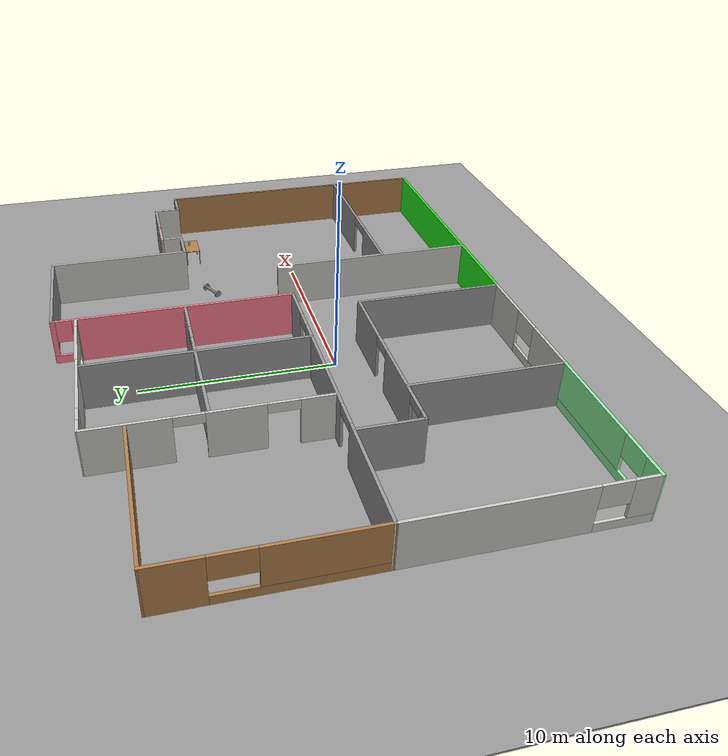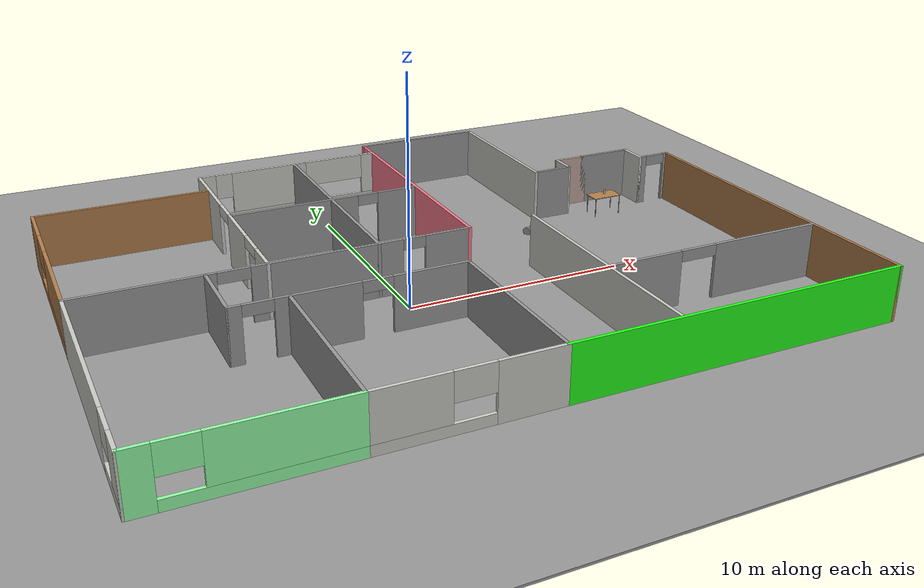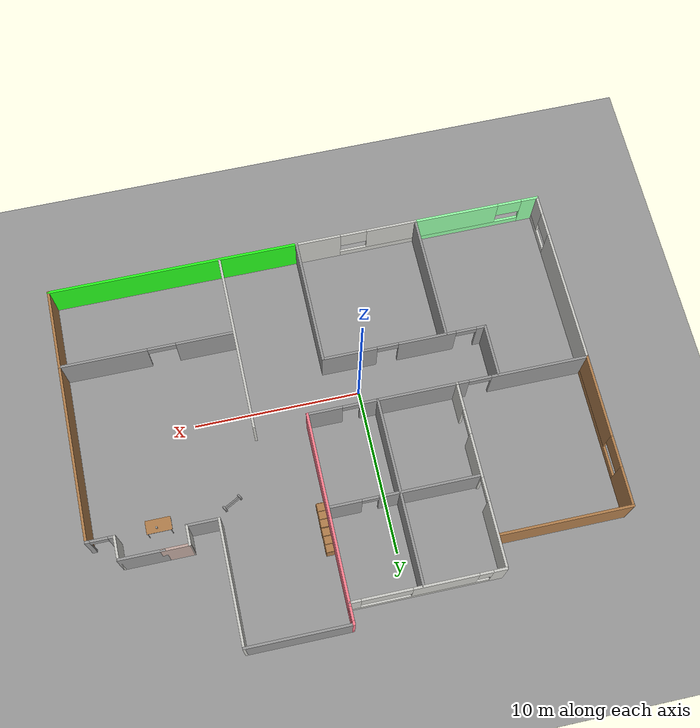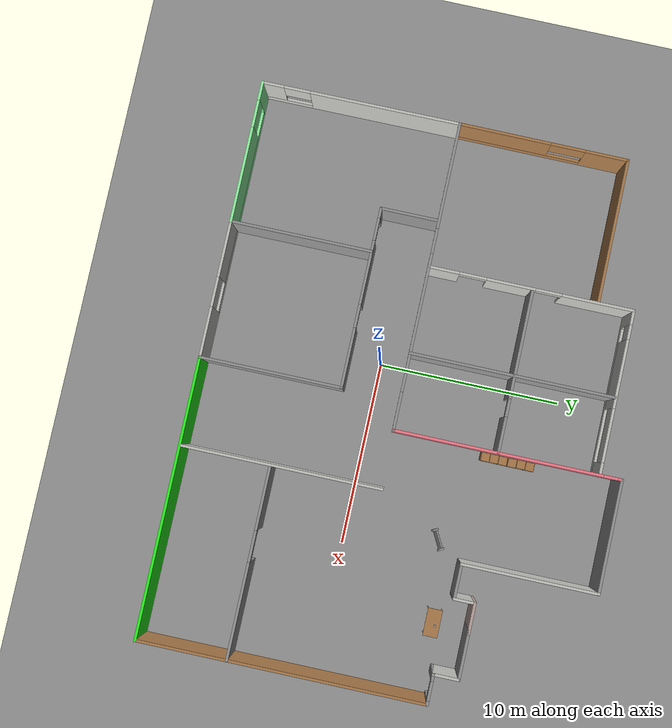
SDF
<sdf version="1.6">
 <world name="default">
  <plugin name="hello" filename="libhello.so"/>
  <light name="sun" type="directional">
   <pose>0 0 10 0 -0 0</pose>
   <diffuse>0.8 0.8 0.8 1</diffuse>
   <specular>0.2 0.2 0.2 1</specular>
   <attenuation>
    <range>1000</range>
    <constant>0.9</constant>
    <linear>0.01</linear>
    <quadratic>0.001</quadratic>
   </attenuation>
   <direction>-0.5 0.1 -0.9</direction>
  </light>
  <model name="ground_plane">
   <static>1</static>
   <link name="link">
    <collision name="collision">
     <geometry><plane><normal>0 0 1</normal><size>100 100</size></plane></geometry>
     <surface>
      <contact><collide_bitmask>65535</collide_bitmask></contact>
      <friction><ode><mu>100</mu><mu2>50</mu2></ode></friction>
     </surface>
    </collision>
    <visual name="visual">
     <cast_shadows>0</cast_shadows>
     <geometry><plane><normal>0 0 1</normal><size>100 100</size></plane></geometry>
     <material>
      <script><uri>file://media/materials/scripts/gazebo.material</uri><name>Gazebo/Grey</name></script>
     </material>
    </visual>
   </link>
  </model>
  <gravity>0 0 -9.8</gravity>
  <magnetic_field>6e-06 2.3e-05 -4.2e-05</magnetic_field>
  <atmosphere type="adiabatic"/>
  <physics name="default_physics" default="0" type="ode">
   <max_step_size>0.001</max_step_size>
   <real_time_factor>1</real_time_factor>
   <real_time_update_rate>1000</real_time_update_rate>
  </physics>
  <scene><ambient>0.4 0.4 0.4 1</ambient><background>0.7 0.7 0.7 1</background><shadows>1</shadows></scene>
  <spherical_coordinates>
   <surface_model>EARTH_WGS84</surface_model>
   <latitude_deg>0</latitude_deg>
   <longitude_deg>0</longitude_deg>
   <elevation>0</elevation>
   <heading_deg>0</heading_deg>
  </spherical_coordinates>
  <model name="robot">
   <link name="link_0">
    <inertial>
     <mass>1</mass>
     <inertia>
      <ixx>0.166667</ixx>
      <ixy>0</ixy>
      <ixz>0</ixz>
      <iyy>0.166667</iyy>
      <iyz>0</iyz>
      <izz>0.166667</izz>
     </inertia>
     <pose>0 0 0.2 0 -0 0</pose>
    </inertial>
    <visual name="visual">
     <geometry><box><size>0.3 1 0.1</size></box></geometry>
     <material>
      <lighting>1</lighting>
      <script><uri>file://media/materials/scripts/gazebo.material</uri><name>Gazebo/Grey</name></script>
      <shader type="pixel"><normal_map>__default__</normal_map></shader>
      <ambient>0.3 0.3 0.3 1</ambient>
      <diffuse>0.7 0.7 0.7 1</diffuse>
      <specular>0.01 0.01 0.01 1</specular>
      <emissive>0 0 0 1</emissive>
     </material>
    </visual>
    <collision name="collision">
     <geometry><box><size>0.3 1 0.1</size></box></geometry>
     <surface>
      <friction>
       <ode><mu>1</mu><mu2>1</mu2><fdir1>0 0 0</fdir1><slip1>0</slip1><slip2>0</slip2></ode>
       <torsional>
        <coefficient>1</coefficient>
        <patch_radius>0</patch_radius>
        <surface_radius>0</surface_radius>
        <use_patch_radius>1</use_patch_radius>
        <ode><slip>0</slip></ode>
       </torsional>
      </friction>
      <bounce><restitution_coefficient>0</restitution_coefficient><threshold>1e+06</threshold></bounce>
      <contact>
       <collide_without_contact>0</collide_without_contact>
       <collide_without_contact_bitmask>1</collide_without_contact_bitmask>
       <collide_bitmask>1</collide_bitmask>
       <ode>
        <soft_cfm>0</soft_cfm>
        <soft_erp>0.2</soft_erp>
        <kp>1e+13</kp>
        <kd>1</kd>
        <max_vel>0.01</max_vel>
        <min_depth>0</min_depth>
       </ode>
       <bullet>
        <split_impulse>1</split_impulse>
        <split_impulse_penetration_threshold>-0.01</split_impulse_penetration_threshold>
        <soft_cfm>0</soft_cfm>
        <soft_erp>0.2</soft_erp>
        <kp>1e+13</kp>
        <kd>1</kd>
       </bullet>
      </contact>
     </surface>
    </collision>
   </link>
   <link name="link_2">
    <pose>0 -0.550019 0 1.5707 -0 0</pose>
    <inertial>
     <mass>1</mass>
     <inertia><ixx>0.145833</ixx><ixy>0</ixy><ixz>0</ixz><iyy>0.145833</iyy><iyz>0</iyz><izz>0.125</izz></inertia>
    </inertial>
    <visual name="visual">
     <geometry><cylinder><radius>0.2</radius><length>0.1</length></cylinder></geometry>
     <material>
      <lighting>1</lighting>
      <script><uri>file://media/materials/scripts/gazebo.material</uri><name>Gazebo/Grey</name></script>
      <shader type="pixel"><normal_map>__default__</normal_map></shader>
      <ambient>0.3 0.3 0.3 1</ambient>
      <diffuse>0.7 0.7 0.7 1</diffuse>
      <specular>0.01 0.01 0.01 1</specular>
      <emissive>0 0 0 1</emissive>
     </material>
    </visual>
    <collision name="collision">
     <geometry><cylinder><radius>0.2</radius><length>0.1</length></cylinder></geometry>
     <surface>
      <friction>
       <ode><mu>1</mu><mu2>1</mu2><fdir1>0 0 0</fdir1><slip1>0</slip1><slip2>0</slip2></ode>
       <torsional>
        <coefficient>1</coefficient>
        <patch_radius>0</patch_radius>
        <surface_radius>0</surface_radius>
        <use_patch_radius>1</use_patch_radius>
        <ode><slip>0</slip></ode>
       </torsional>
      </friction>
      <bounce><restitution_coefficient>0</restitution_coefficient><threshold>1e+06</threshold></bounce>
      <contact>
       <collide_without_contact>0</collide_without_contact>
       <collide_without_contact_bitmask>1</collide_without_contact_bitmask>
       <collide_bitmask>1</collide_bitmask>
       <ode>
        <soft_cfm>0</soft_cfm>
        <soft_erp>0.2</soft_erp>
        <kp>1e+13</kp>
        <kd>1</kd>
        <max_vel>0.01</max_vel>
        <min_depth>0</min_depth>
       </ode>
       <bullet>
        <split_impulse>1</split_impulse>
        <split_impulse_penetration_threshold>-0.01</split_impulse_penetration_threshold>
        <soft_cfm>0</soft_cfm>
        <soft_erp>0.2</soft_erp>
        <kp>1e+13</kp>
        <kd>1</kd>
       </bullet>
      </contact>
     </surface>
    </collision>
   </link>
   <link name="link_2_clone">
    <pose>0 0.550019 0 1.5707 -0 0</pose>
    <inertial>
     <mass>1</mass>
     <inertia><ixx>0.145833</ixx><ixy>0</ixy><ixz>0</ixz><iyy>0.145833</iyy><iyz>0</iyz><izz>0.125</izz></inertia>
    </inertial>
    <visual name="visual">
     <geometry><cylinder><radius>0.2</radius><length>0.1</length></cylinder></geometry>
     <material>
      <lighting>1</lighting>
      <script><uri>file://media/materials/scripts/gazebo.material</uri><name>Gazebo/Grey</name></script>
      <shader type="pixel"><normal_map>__default__</normal_map></shader>
      <ambient>0.3 0.3 0.3 1</ambient>
      <diffuse>0.7 0.7 0.7 1</diffuse>
      <specular>0.01 0.01 0.01 1</specular>
      <emissive>0 0 0 1</emissive>
     </material>
    </visual>
    <collision name="collision">
     <geometry><cylinder><radius>0.2</radius><length>0.1</length></cylinder></geometry>
     <surface>
      <friction>
       <ode><mu>1</mu><mu2>1</mu2><fdir1>0 0 0</fdir1><slip1>0</slip1><slip2>0</slip2></ode>
       <torsional>
        <coefficient>1</coefficient>
        <patch_radius>0</patch_radius>
        <surface_radius>0</surface_radius>
        <use_patch_radius>1</use_patch_radius>
        <ode><slip>0</slip></ode>
       </torsional>
      </friction>
      <bounce><restitution_coefficient>0</restitution_coefficient><threshold>1e+06</threshold></bounce>
      <contact>
       <collide_without_contact>0</collide_without_contact>
       <collide_without_contact_bitmask>1</collide_without_contact_bitmask>
       <collide_bitmask>1</collide_bitmask>
       <ode>
        <soft_cfm>0</soft_cfm>
        <soft_erp>0.2</soft_erp>
        <kp>1e+13</kp>
        <kd>1</kd>
        <max_vel>0.01</max_vel>
        <min_depth>0</min_depth>
       </ode>
       <bullet>
        <split_impulse>1</split_impulse>
        <split_impulse_penetration_threshold>-0.01</split_impulse_penetration_threshold>
        <soft_cfm>0</soft_cfm>
        <soft_erp>0.2</soft_erp>
        <kp>1e+13</kp>
        <kd>1</kd>
       </bullet>
      </contact>
     </surface>
    </collision>
   </link>
   <joint name="link_0_JOINT_0" type="revolute">
    <parent>link_0</parent>
    <child>link_2</child>
    <axis>
     <xyz>0 0 1</xyz>
     <use_parent_model_frame>0</use_parent_model_frame>
     <limit>
      <lower>-1.79769e+308</lower>
      <upper>1.79769e+308</upper>
      <effort>-1</effort>
      <velocity>-1</velocity>
     </limit>
     <dynamics>
      <spring_reference>0</spring_reference>
      <spring_stiffness>0</spring_stiffness>
      <damping>0</damping>
     </dynamics>
    </axis>
    <physics>
     <ode><limit><cfm>0</cfm><erp>0.2</erp></limit><suspension><cfm>0</cfm><erp>0.2</erp></suspension></ode>
    </physics>
   </joint>
   <joint name="link_0_JOINT_1" type="revolute">
    <parent>link_0</parent>
    <child>link_2_clone</child>
    <axis>
     <xyz>0 0 1</xyz>
     <use_parent_model_frame>0</use_parent_model_frame>
     <limit>
      <lower>-1.79769e+308</lower>
      <upper>1.79769e+308</upper>
      <effort>-1</effort>
      <velocity>-1</velocity>
     </limit>
     <dynamics>
      <spring_reference>0</spring_reference>
      <spring_stiffness>0</spring_stiffness>
      <damping>0</damping>
      <friction>0</friction>
     </dynamics>
    </axis>
    <physics>
     <ode><limit><cfm>0</cfm><erp>0.2</erp></limit><suspension><cfm>0</cfm><erp>0.2</erp></suspension></ode>
    </physics>
   </joint>
   <static>0</static>
   <pose>8.70943 5.10488 0.200001 5e-06 1.0012 -1.07385</pose>
  </model>
  <model name="ground_plane_0">
   <static>1</static>
   <link name="link">
    <collision name="collision">
     <geometry><plane><normal>0 0 1</normal><size>100 100</size></plane></geometry>
     <surface>
      <contact><collide_bitmask>65535</collide_bitmask></contact>
      <friction><ode><mu>100</mu><mu2>50</mu2></ode></friction>
     </surface>
    </collision>
    <visual name="visual">
     <cast_shadows>0</cast_shadows>
     <geometry><plane><normal>0 0 1</normal><size>100 100</size></plane></geometry>
     <material>
      <script><uri>file://media/materials/scripts/gazebo.material</uri><name>Gazebo/Grey</name></script>
     </material>
    </visual>
   </link>
   <pose>0.029659 0.113725 0 0 -0 0</pose>
  </model>
  <model name="myhome">
   <pose>1.8142 2.19127 0 0 -0 0</pose>
   <link name="Wall_0">
    <collision name="Wall_0_Collision">
     <geometry><box><size>2.75 0.15 2.5</size></box></geometry>
     <pose>0 0 1.25 0 -0 0</pose>
    </collision>
    <visual name="Wall_0_Visual">
     <pose>0 0 1.25 0 -0 0</pose>
     <geometry><box><size>2.75 0.15 2.5</size></box></geometry>
     <material>
      <script><uri>file://media/materials/scripts/gazebo.material</uri><name>Gazebo/Grey</name></script>
      <ambient>1 1 1 1</ambient>
     </material>
     <meta><layer>0</layer></meta>
    </visual>
    <pose>12.3251 5.36908 0 0 -0 0</pose>
   </link>
   <link name="Wall_1">
    <collision name="Wall_1_Collision">
     <geometry><box><size>1.5 0.15 2.5</size></box></geometry>
     <pose>0 0 1.25 0 -0 0</pose>
    </collision>
    <visual name="Wall_1_Visual">
     <pose>0 0 1.25 0 -0 0</pose>
     <geometry><box><size>1.5 0.15 2.5</size></box></geometry>
     <material>
      <script><uri>file://media/materials/scripts/gazebo.material</uri><name>Gazebo/CeilingTiled</name></script>
      <ambient>1 1 1 1</ambient>
     </material>
     <meta><layer>0</layer></meta>
    </visual>
    <pose>13.6251 4.69408 0 0 0 -1.5708</pose>
   </link>
   <link name="Wall_10">
    <collision name="Wall_10_Collision">
     <geometry><box><size>7.5 0.15 2.5</size></box></geometry>
     <pose>0 0 1.25 0 -0 0</pose>
    </collision>
    <visual name="Wall_10_Visual">
     <pose>0 0 1.25 0 -0 0</pose>
     <geometry><box><size>7.5 0.15 2.5</size></box></geometry>
     <material>
      <script><uri>file://media/materials/scripts/gazebo.material</uri><name>Gazebo/CeilingTiled</name></script>
      <ambient>1 1 1 1</ambient>
     </material>
     <meta><layer>0</layer></meta>
    </visual>
    <pose>7.72467 7.93597 0 0 0 -1.5708</pose>
   </link>
   <link name="Wall_11">
    <collision name="Wall_11_Collision">
     <geometry><box><size>2 0.15 2.5</size></box></geometry>
     <pose>0 0 1.25 0 -0 0</pose>
    </collision>
    <visual name="Wall_11_Visual">
     <pose>0 0 1.25 0 -0 0</pose>
     <geometry><box><size>2 0.15 2.5</size></box></geometry>
     <material>
      <script><uri>file://media/materials/scripts/gazebo.material</uri><name>Gazebo/Grey</name></script>
      <ambient>1 1 1 1</ambient>
     </material>
     <meta><layer>0</layer></meta>
    </visual>
    <pose>8.64967 4.26097 0 0 -0 0</pose>
   </link>
   <link name="Wall_12">
    <collision name="Wall_12_Collision">
     <geometry><box><size>1.25811 0.15 2.5</size></box></geometry>
     <pose>0 0 1.25 0 -0 0</pose>
    </collision>
    <visual name="Wall_12_Visual">
     <pose>0 0 1.25 0 -0 0</pose>
     <geometry><box><size>1.25811 0.15 2.5</size></box></geometry>
     <material>
      <script><uri>file://media/materials/scripts/gazebo.material</uri><name>Gazebo/CeilingTiled</name></script>
      <ambient>1 1 1 1</ambient>
     </material>
     <meta><layer>0</layer></meta>
    </visual>
    <pose>9.5749 4.81502 0 0 -0 1.57038</pose>
   </link>
   <link name="Wall_13">
    <collision name="Wall_13_Collision">
     <geometry><box><size>1.75 0.15 2.5</size></box></geometry>
     <pose>0 0 1.25 0 -0 0</pose>
    </collision>
    <visual name="Wall_13_Visual">
     <pose>0 0 1.25 0 -0 0</pose>
     <geometry><box><size>1.75 0.15 2.5</size></box></geometry>
     <material>
      <script><uri>file://media/materials/scripts/gazebo.material</uri><name>Gazebo/Grey</name></script>
      <ambient>0.760784 0.662745 0.627451 1</ambient>
     </material>
     <meta><layer>0</layer></meta>
    </visual>
    <pose>10.3751 5.36908 0 0 -0 0</pose>
   </link>
   <link name="Wall_17">
    <pose>-6.8051 -0.738977 0 0 0 -3.14159</pose>
    <visual name="Wall_17_Visual_0">
     <pose>-7.4168 0 1.25 0 -0 0</pose>
     <geometry><box><size>2.15686 0.15 2.5</size></box></geometry>
     <material>
      <script><uri>file://media/materials/scripts/gazebo.material</uri><name>Gazebo/Grey</name></script>
      <ambient>1 1 1 1</ambient>
     </material>
     <meta><layer>0</layer></meta>
    </visual>
    <collision name="Wall_17_Collision_0">
     <geometry><box><size>2.15686 0.15 2.5</size></box></geometry>
     <pose>-7.4168 0 1.25 0 -0 0</pose>
    </collision>
    <visual name="Wall_17_Visual_1">
     <pose>-2.04089 0 1.25 0 -0 0</pose>
     <geometry><box><size>6.55161 0.15 2.5</size></box></geometry>
     <material>
      <script><uri>file://media/materials/scripts/gazebo.material</uri><name>Gazebo/Grey</name></script>
      <ambient>1 1 1 1</ambient>
     </material>
     <meta><layer>0</layer></meta>
    </visual>
    <collision name="Wall_17_Collision_1">
     <geometry><box><size>6.55161 0.15 2.5</size></box></geometry>
     <pose>-2.04089 0 1.25 0 -0 0</pose>
    </collision>
    <visual name="Wall_17_Visual_2">
     <pose>5.54911 0 1.25 0 -0 0</pose>
     <geometry><box><size>5.89224 0.15 2.5</size></box></geometry>
     <material>
      <script><uri>file://media/materials/scripts/gazebo.material</uri><name>Gazebo/Grey</name></script>
      <ambient>1 1 1 1</ambient>
     </material>
     <meta><layer>0</layer></meta>
    </visual>
    <collision name="Wall_17_Collision_2">
     <geometry><box><size>5.89224 0.15 2.5</size></box></geometry>
     <pose>5.54911 0 1.25 0 -0 0</pose>
    </collision>
    <visual name="Wall_17_Visual_3">
     <pose>-5.82753 0 2.25 0 -0 0</pose>
     <geometry><box><size>1.02167 0.15 0.5</size></box></geometry>
     <material>
      <script><uri>file://media/materials/scripts/gazebo.material</uri><name>Gazebo/Grey</name></script>
      <ambient>1 1 1 1</ambient>
     </material>
     <meta><layer>0</layer></meta>
    </visual>
    <collision name="Wall_17_Collision_3">
     <geometry><box><size>1.02167 0.15 0.5</size></box></geometry>
     <pose>-5.82753 0 2.25 0 -0 0</pose>
    </collision>
    <visual name="Wall_17_Visual_4">
     <pose>1.91895 0 2.25 0 -0 0</pose>
     <geometry><box><size>1.36808 0.15 0.5</size></box></geometry>
     <material>
      <script><uri>file://media/materials/scripts/gazebo.material</uri><name>Gazebo/Grey</name></script>
      <ambient>1 1 1 1</ambient>
     </material>
     <meta><layer>0</layer></meta>
    </visual>
    <collision name="Wall_17_Collision_4">
     <geometry><box><size>1.36808 0.15 0.5</size></box></geometry>
     <pose>1.91895 0 2.25 0 -0 0</pose>
    </collision>
   </link>
   <link name="Wall_2">
    <pose>14.4251 4.01908 0 0 -0 0</pose>
    <visual name="Wall_2_Visual_0">
     <pose>-0.659805 0 1.25 0 -0 0</pose>
     <geometry><box><size>0.43039 0.15 2.5</size></box></geometry>
     <material>
      <script><uri>file://media/materials/scripts/gazebo.material</uri><name>Gazebo/Grey</name></script>
      <ambient>1 1 1 1</ambient>
     </material>
     <meta><layer>0</layer></meta>
    </visual>
    <collision name="Wall_2_Collision_0">
     <geometry><box><size>0.43039 0.15 2.5</size></box></geometry>
     <pose>-0.659805 0 1.25 0 -0 0</pose>
    </collision>
    <visual name="Wall_2_Visual_1">
     <pose>0.733934 0 1.25 0 -0 0</pose>
     <geometry><box><size>0.282132 0.15 2.5</size></box></geometry>
     <material>
      <script><uri>file://media/materials/scripts/gazebo.material</uri><name>Gazebo/Grey</name></script>
      <ambient>1 1 1 1</ambient>
     </material>
     <meta><layer>0</layer></meta>
    </visual>
    <collision name="Wall_2_Collision_1">
     <geometry><box><size>0.282132 0.15 2.5</size></box></geometry>
     <pose>0.733934 0 1.25 0 -0 0</pose>
    </collision>
    <visual name="Wall_2_Visual_2">
     <pose>0.074129 0 2.25 0 -0 0</pose>
     <geometry><box><size>1.03748 0.15 0.5</size></box></geometry>
     <material>
      <script><uri>file://media/materials/scripts/gazebo.material</uri><name>Gazebo/Grey</name></script>
      <ambient>1 1 1 1</ambient>
     </material>
     <meta><layer>0</layer></meta>
    </visual>
    <collision name="Wall_2_Collision_2">
     <geometry><box><size>1.03748 0.15 0.5</size></box></geometry>
     <pose>0.074129 0 2.25 0 -0 0</pose>
    </collision>
   </link>
   <link name="Wall_20">
    <pose>-11.329 -11.6109 0 0 -0 0</pose>
    <visual name="Wall_20_Visual_0">
     <pose>-3.40478 0 1.25 0 -0 0</pose>
     <geometry><box><size>1.08011 0.15 2.5</size></box></geometry>
     <material>
      <script><uri>file://media/materials/scripts/gazebo.material</uri><name>Gazebo/Grey</name></script>
      <ambient>0.584314 1 0.654902 1</ambient>
     </material>
     <meta><layer>0</layer></meta>
    </visual>
    <collision name="Wall_20_Collision_0">
     <geometry><box><size>1.08011 0.15 2.5</size></box></geometry>
     <pose>-3.40478 0 1.25 0 -0 0</pose>
    </collision>
    <visual name="Wall_20_Visual_1">
     <pose>0.540053 0 0.25 0 -0 0</pose>
     <geometry><box><size>6.80957 0.15 0.5</size></box></geometry>
     <material>
      <script><uri>file://media/materials/scripts/gazebo.material</uri><name>Gazebo/Grey</name></script>
      <ambient>0.584314 1 0.654902 1</ambient>
     </material>
     <meta><layer>0</layer></meta>
    </visual>
    <collision name="Wall_20_Collision_1">
     <geometry><box><size>6.80957 0.15 0.5</size></box></geometry>
     <pose>0.540053 0 0.25 0 -0 0</pose>
    </collision>
    <visual name="Wall_20_Visual_2">
     <pose>1.29073 0 1.5 0 -0 0</pose>
     <geometry><box><size>5.30822 0.15 2</size></box></geometry>
     <material>
      <script><uri>file://media/materials/scripts/gazebo.material</uri><name>Gazebo/Grey</name></script>
      <ambient>0.584314 1 0.654902 1</ambient>
     </material>
     <meta><layer>0</layer></meta>
    </visual>
    <collision name="Wall_20_Collision_2">
     <geometry><box><size>5.30822 0.15 2</size></box></geometry>
     <pose>1.29073 0 1.5 0 -0 0</pose>
    </collision>
    <visual name="Wall_20_Visual_3">
     <pose>-2.11406 0 1.9 0 -0 0</pose>
     <geometry><box><size>1.50135 0.15 1.2</size></box></geometry>
     <material>
      <script><uri>file://media/materials/scripts/gazebo.material</uri><name>Gazebo/Grey</name></script>
      <ambient>0.584314 1 0.654902 1</ambient>
     </material>
     <meta><layer>0</layer></meta>
    </visual>
    <collision name="Wall_20_Collision_3">
     <geometry><box><size>1.50135 0.15 1.2</size></box></geometry>
     <pose>-2.11406 0 1.9 0 -0 0</pose>
    </collision>
   </link>
   <link name="Wall_21">
    <collision name="Wall_21_Collision">
     <geometry><box><size>7.75 0.15 2.5</size></box></geometry>
     <pose>0 0 1.25 0 -0 0</pose>
    </collision>
    <visual name="Wall_21_Visual">
     <pose>0 0 1.25 0 -0 0</pose>
     <geometry><box><size>7.75 0.15 2.5</size></box></geometry>
     <material>
      <script><uri>file://media/materials/scripts/gazebo.material</uri><name>Gazebo/Grey</name></script>
      <ambient>1 1 1 1</ambient>
     </material>
     <meta><layer>0</layer></meta>
    </visual>
    <pose>-7.45919 -7.73959 0 0 -0 1.5708</pose>
   </link>
   <link name="Wall_23">
    <collision name="Wall_23_Collision">
     <geometry><box><size>7.84924 0.15 2.5</size></box></geometry>
     <pose>0 0 1.25 0 -0 0</pose>
    </collision>
    <visual name="Wall_23_Visual">
     <pose>0 0 1.25 0 -0 0</pose>
     <geometry><box><size>7.84924 0.15 2.5</size></box></geometry>
     <material>
      <script><uri>file://media/materials/scripts/gazebo.material</uri><name>Gazebo/Grey</name></script>
      <ambient>1 1 1 1</ambient>
     </material>
     <meta><layer>0</layer></meta>
    </visual>
    <pose>0.005135 -7.76092 0 0 0 -1.5708</pose>
   </link>
   <link name="Wall_24">
    <pose>-3.72703 -11.6109 0 0 -0 3.14159</pose>
    <visual name="Wall_24_Visual_0">
     <pose>-2.39823 0 1.25 0 -0 0</pose>
     <geometry><box><size>2.81787 0.15 2.5</size></box></geometry>
     <material>
      <script><uri>file://media/materials/scripts/gazebo.material</uri><name>Gazebo/CeilingTiled</name></script>
      <ambient>1 1 1 1</ambient>
     </material>
     <meta><layer>0</layer></meta>
    </visual>
    <collision name="Wall_24_Collision_0">
     <geometry><box><size>2.81787 0.15 2.5</size></box></geometry>
     <pose>-2.39823 0 1.25 0 -0 0</pose>
    </collision>
    <visual name="Wall_24_Visual_1">
     <pose>1.40893 0 0.25 0 -0 0</pose>
     <geometry><box><size>4.79646 0.15 0.5</size></box></geometry>
     <material>
      <script><uri>file://media/materials/scripts/gazebo.material</uri><name>Gazebo/CeilingTiled</name></script>
      <ambient>1 1 1 1</ambient>
     </material>
     <meta><layer>0</layer></meta>
    </visual>
    <collision name="Wall_24_Collision_1">
     <geometry><box><size>4.79646 0.15 0.5</size></box></geometry>
     <pose>1.40893 0 0.25 0 -0 0</pose>
    </collision>
    <visual name="Wall_24_Visual_2">
     <pose>2.22974 0 1.5 0 -0 0</pose>
     <geometry><box><size>3.15484 0.15 2</size></box></geometry>
     <material>
      <script><uri>file://media/materials/scripts/gazebo.material</uri><name>Gazebo/CeilingTiled</name></script>
      <ambient>1 1 1 1</ambient>
     </material>
     <meta><layer>0</layer></meta>
    </visual>
    <collision name="Wall_24_Collision_2">
     <geometry><box><size>3.15484 0.15 2</size></box></geometry>
     <pose>2.22974 0 1.5 0 -0 0</pose>
    </collision>
    <visual name="Wall_24_Visual_3">
     <pose>-0.168486 0 1.9 0 -0 0</pose>
     <geometry><box><size>1.64162 0.15 1.2</size></box></geometry>
     <material>
      <script><uri>file://media/materials/scripts/gazebo.material</uri><name>Gazebo/CeilingTiled</name></script>
      <ambient>1 1 1 1</ambient>
     </material>
     <meta><layer>0</layer></meta>
    </visual>
    <collision name="Wall_24_Collision_3">
     <geometry><box><size>1.64162 0.15 1.2</size></box></geometry>
     <pose>-0.168486 0 1.9 0 -0 0</pose>
    </collision>
   </link>
   <link name="Wall_26">
    <collision name="Wall_26_Collision">
     <geometry><box><size>8 0.15 2.5</size></box></geometry>
     <pose>0 0 1.25 0 -0 0</pose>
    </collision>
    <visual name="Wall_26_Visual">
     <pose>0 0 1.25 0 -0 0</pose>
     <geometry><box><size>8 0.15 2.5</size></box></geometry>
     <material>
      <script><uri>file://media/materials/scripts/gazebo.material</uri><name>Gazebo/Wood</name></script>
      <ambient>1 1 1 1</ambient>
     </material>
     <meta><layer>0</layer></meta>
    </visual>
    <pose>-11.2739 8.48908 0 0 -0 0</pose>
   </link>
   <link name="Wall_29">
    <pose>-7.32018 4.81097 0 0 0 -1.5708</pose>
    <visual name="Wall_29_Visual_0">
     <pose>-3.65679 0 1.25 0 -0 0</pose>
     <geometry><box><size>3.93643 0.15 2.5</size></box></geometry>
     <material>
      <script><uri>file://media/materials/scripts/gazebo.material</uri><name>Gazebo/CeilingTiled</name></script>
      <ambient>1 1 1 1</ambient>
     </material>
     <meta><layer>0</layer></meta>
    </visual>
    <collision name="Wall_29_Collision_0">
     <geometry><box><size>3.93643 0.15 2.5</size></box></geometry>
     <pose>-3.65679 0 1.25 0 -0 0</pose>
    </collision>
    <visual name="Wall_29_Visual_1">
     <pose>1.0605 0 1.25 0 -0 0</pose>
     <geometry><box><size>2.67803 0.15 2.5</size></box></geometry>
     <material>
      <script><uri>file://media/materials/scripts/gazebo.material</uri><name>Gazebo/CeilingTiled</name></script>
      <ambient>1 1 1 1</ambient>
     </material>
     <meta><layer>0</layer></meta>
    </visual>
    <collision name="Wall_29_Collision_1">
     <geometry><box><size>2.67803 0.15 2.5</size></box></geometry>
     <pose>1.0605 0 1.25 0 -0 0</pose>
    </collision>
    <visual name="Wall_29_Visual_2">
     <pose>4.75554 0 1.25 0 -0 0</pose>
     <geometry><box><size>1.73892 0.15 2.5</size></box></geometry>
     <material>
      <script><uri>file://media/materials/scripts/gazebo.material</uri><name>Gazebo/CeilingTiled</name></script>
      <ambient>1 1 1 1</ambient>
     </material>
     <meta><layer>0</layer></meta>
    </visual>
    <collision name="Wall_29_Collision_2">
     <geometry><box><size>1.73892 0.15 2.5</size></box></geometry>
     <pose>4.75554 0 1.25 0 -0 0</pose>
    </collision>
    <visual name="Wall_29_Visual_3">
     <pose>-0.983543 0 2.25 0 -0 0</pose>
     <geometry><box><size>1.41006 0.15 0.5</size></box></geometry>
     <material>
      <script><uri>file://media/materials/scripts/gazebo.material</uri><name>Gazebo/CeilingTiled</name></script>
      <ambient>1 1 1 1</ambient>
     </material>
     <meta><layer>0</layer></meta>
    </visual>
    <collision name="Wall_29_Collision_3">
     <geometry><box><size>1.41006 0.15 0.5</size></box></geometry>
     <pose>-0.983543 0 2.25 0 -0 0</pose>
    </collision>
    <visual name="Wall_29_Visual_4">
     <pose>3.1428 0 2.25 0 -0 0</pose>
     <geometry><box><size>1.48656 0.15 0.5</size></box></geometry>
     <material>
      <script><uri>file://media/materials/scripts/gazebo.material</uri><name>Gazebo/CeilingTiled</name></script>
      <ambient>1 1 1 1</ambient>
     </material>
     <meta><layer>0</layer></meta>
    </visual>
    <collision name="Wall_29_Collision_4">
     <geometry><box><size>1.48656 0.15 0.5</size></box></geometry>
     <pose>3.1428 0 2.25 0 -0 0</pose>
    </collision>
   </link>
   <link name="Wall_31">
    <pose>-2.79237 4.93708 0 0 -0 0</pose>
    <visual name="Wall_31_Visual_0">
     <pose>-1.50721 0 1.25 0 -0 0</pose>
     <geometry><box><size>5.95058 0.15 2.5</size></box></geometry>
     <material>
      <script><uri>file://media/materials/scripts/gazebo.material</uri><name>Gazebo/Grey</name></script>
      <ambient>1 1 1 1</ambient>
     </material>
     <meta><layer>0</layer></meta>
    </visual>
    <collision name="Wall_31_Collision_0">
     <geometry><box><size>5.95058 0.15 2.5</size></box></geometry>
     <pose>-1.50721 0 1.25 0 -0 0</pose>
    </collision>
    <visual name="Wall_31_Visual_1">
     <pose>3.46585 0 1.25 0 -0 0</pose>
     <geometry><box><size>2.0333 0.15 2.5</size></box></geometry>
     <material>
      <script><uri>file://media/materials/scripts/gazebo.material</uri><name>Gazebo/Grey</name></script>
      <ambient>1 1 1 1</ambient>
     </material>
     <meta><layer>0</layer></meta>
    </visual>
    <collision name="Wall_31_Collision_1">
     <geometry><box><size>2.0333 0.15 2.5</size></box></geometry>
     <pose>3.46585 0 1.25 0 -0 0</pose>
    </collision>
    <visual name="Wall_31_Visual_2">
     <pose>1.95864 0 2.25 0 -0 0</pose>
     <geometry><box><size>0.981113 0.15 0.5</size></box></geometry>
     <material>
      <script><uri>file://media/materials/scripts/gazebo.material</uri><name>Gazebo/Grey</name></script>
      <ambient>1 1 1 1</ambient>
     </material>
     <meta><layer>0</layer></meta>
    </visual>
    <collision name="Wall_31_Collision_2">
     <geometry><box><size>0.981113 0.15 0.5</size></box></geometry>
     <pose>1.95864 0 2.25 0 -0 0</pose>
    </collision>
   </link>
   <link name="Wall_33">
    <collision name="Wall_33_Collision">
     <geometry><box><size>15.78 0.15 2.5</size></box></geometry>
     <pose>0 0 1.25 0 -0 0</pose>
    </collision>
    <visual name="Wall_33_Visual">
     <pose>0 0 1.25 0 -0 0</pose>
     <geometry><box><size>15.78 0.15 2.5</size></box></geometry>
     <material>
      <script><uri>file://media/materials/scripts/gazebo.material</uri><name>Gazebo/Wood</name></script>
      <ambient>1 1 1 1</ambient>
     </material>
     <meta><layer>0</layer></meta>
    </visual>
    <pose>15.2251 -3.79592 0 0 0 -1.5708</pose>
   </link>
   <link name="Wall_34">
    <collision name="Wall_34_Collision">
     <geometry><box><size>15.3708 0.15 2.5</size></box></geometry>
     <pose>0 0 1.25 0 -0 0</pose>
    </collision>
    <visual name="Wall_34_Visual">
     <pose>0 0 1.25 0 -0 0</pose>
     <geometry><box><size>15.3708 0.15 2.5</size></box></geometry>
     <material>
      <script><uri>file://media/materials/scripts/gazebo.material</uri><name>Gazebo/Grey</name></script>
      <ambient>0.152941 1 0.109804 1</ambient>
     </material>
     <meta><layer>0</layer></meta>
    </visual>
    <pose>7.61514 -11.6109 0 0 -0 3.14159</pose>
   </link>
   <link name="Wall_36">
    <pose>-4.91986 -3.91092 0 0 -0 0</pose>
    <visual name="Wall_36_Visual_0">
     <pose>-4.69801 0 1.25 0 -0 0</pose>
     <geometry><box><size>0.603972 0.15 2.5</size></box></geometry>
     <material>
      <script><uri>file://media/materials/scripts/gazebo.material</uri><name>Gazebo/Grey</name></script>
      <ambient>1 1 1 1</ambient>
     </material>
     <meta><layer>0</layer></meta>
    </visual>
    <collision name="Wall_36_Collision_0">
     <geometry><box><size>0.603972 0.15 2.5</size></box></geometry>
     <pose>-4.69801 0 1.25 0 -0 0</pose>
    </collision>
    <visual name="Wall_36_Visual_1">
     <pose>-1.39103 0 1.25 0 -0 0</pose>
     <geometry><box><size>3.50788 0.15 2.5</size></box></geometry>
     <material>
      <script><uri>file://media/materials/scripts/gazebo.material</uri><name>Gazebo/Grey</name></script>
      <ambient>1 1 1 1</ambient>
     </material>
     <meta><layer>0</layer></meta>
    </visual>
    <collision name="Wall_36_Collision_1">
     <geometry><box><size>3.50788 0.15 2.5</size></box></geometry>
     <pose>-1.39103 0 1.25 0 -0 0</pose>
    </collision>
    <visual name="Wall_36_Visual_2">
     <pose>3.32649 0 1.25 0 -0 0</pose>
     <geometry><box><size>3.34702 0.15 2.5</size></box></geometry>
     <material>
      <script><uri>file://media/materials/scripts/gazebo.material</uri><name>Gazebo/Grey</name></script>
      <ambient>1 1 1 1</ambient>
     </material>
     <meta><layer>0</layer></meta>
    </visual>
    <collision name="Wall_36_Collision_2">
     <geometry><box><size>3.34702 0.15 2.5</size></box></geometry>
     <pose>3.32649 0 1.25 0 -0 0</pose>
    </collision>
    <visual name="Wall_36_Visual_3">
     <pose>-3.7705 0 2.25 0 -0 0</pose>
     <geometry><box><size>1.25106 0.15 0.5</size></box></geometry>
     <material>
      <script><uri>file://media/materials/scripts/gazebo.material</uri><name>Gazebo/Grey</name></script>
      <ambient>1 1 1 1</ambient>
     </material>
     <meta><layer>0</layer></meta>
    </visual>
    <collision name="Wall_36_Collision_3">
     <geometry><box><size>1.25106 0.15 0.5</size></box></geometry>
     <pose>-3.7705 0 2.25 0 -0 0</pose>
    </collision>
    <visual name="Wall_36_Visual_4">
     <pose>1.00795 0 2.25 0 -0 0</pose>
     <geometry><box><size>1.29007 0.15 0.5</size></box></geometry>
     <material>
      <script><uri>file://media/materials/scripts/gazebo.material</uri><name>Gazebo/Grey</name></script>
      <ambient>1 1 1 1</ambient>
     </material>
     <meta><layer>0</layer></meta>
    </visual>
    <collision name="Wall_36_Collision_4">
     <geometry><box><size>1.29007 0.15 0.5</size></box></geometry>
     <pose>1.00795 0 2.25 0 -0 0</pose>
    </collision>
   </link>
   <link name="Wall_38">
    <pose>-15.2121 3.87502 0 0 0 -1.57366</pose>
    <visual name="Wall_38_Visual_0">
     <pose>-3.48833 0 1.25 0 -0 0</pose>
     <geometry><box><size>2.40148 0.15 2.5</size></box></geometry>
     <material>
      <script><uri>file://media/materials/scripts/gazebo.material</uri><name>Gazebo/Wood</name></script>
      <ambient>1 1 1 1</ambient>
     </material>
     <meta><layer>0</layer></meta>
    </visual>
    <collision name="Wall_38_Collision_0">
     <geometry><box><size>2.40148 0.15 2.5</size></box></geometry>
     <pose>-3.48833 0 1.25 0 -0 0</pose>
    </collision>
    <visual name="Wall_38_Visual_1">
     <pose>1.20074 0 0.25 0 -0 0</pose>
     <geometry><box><size>6.97666 0.15 0.5</size></box></geometry>
     <material>
      <script><uri>file://media/materials/scripts/gazebo.material</uri><name>Gazebo/Wood</name></script>
      <ambient>1 1 1 1</ambient>
     </material>
     <meta><layer>0</layer></meta>
    </visual>
    <collision name="Wall_38_Collision_1">
     <geometry><box><size>6.97666 0.15 0.5</size></box></geometry>
     <pose>1.20074 0 0.25 0 -0 0</pose>
    </collision>
    <visual name="Wall_38_Visual_2">
     <pose>2.14428 0 1.5 0 -0 0</pose>
     <geometry><box><size>5.08958 0.15 2</size></box></geometry>
     <material>
      <script><uri>file://media/materials/scripts/gazebo.material</uri><name>Gazebo/Wood</name></script>
      <ambient>1 1 1 1</ambient>
     </material>
     <meta><layer>0</layer></meta>
    </visual>
    <collision name="Wall_38_Collision_2">
     <geometry><box><size>5.08958 0.15 2</size></box></geometry>
     <pose>2.14428 0 1.5 0 -0 0</pose>
    </collision>
    <visual name="Wall_38_Visual_3">
     <pose>-1.34405 0 1.9 0 -0 0</pose>
     <geometry><box><size>1.88709 0.15 1.2</size></box></geometry>
     <material>
      <script><uri>file://media/materials/scripts/gazebo.material</uri><name>Gazebo/Wood</name></script>
      <ambient>1 1 1 1</ambient>
     </material>
     <meta><layer>0</layer></meta>
    </visual>
    <collision name="Wall_38_Collision_3">
     <geometry><box><size>1.88709 0.15 1.2</size></box></geometry>
     <pose>-1.34405 0 1.9 0 -0 0</pose>
    </collision>
   </link>
   <link name="Wall_40">
    <collision name="Wall_40_Collision">
     <geometry><box><size>3.25 0.15 2.5</size></box></geometry>
     <pose>0 0 1.25 0 -0 0</pose>
    </collision>
    <visual name="Wall_40_Visual">
     <pose>0 0 1.25 0 -0 0</pose>
     <geometry><box><size>3.25 0.15 2.5</size></box></geometry>
     <material>
      <script><uri>file://media/materials/scripts/gazebo.material</uri><name>Gazebo/Grey</name></script>
      <ambient>1 1 1 1</ambient>
     </material>
     <meta><layer>0</layer></meta>
    </visual>
    <pose>-9.84487 -2.36092 0 0 -0 1.5708</pose>
   </link>
   <link name="Wall_42">
    <pose>-15.2121 -6.17498 0 0 0 -1.56836</pose>
    <visual name="Wall_42_Visual_0">
     <pose>-1.35271 0 1.25 0 -0 0</pose>
     <geometry><box><size>8.31651 0.15 2.5</size></box></geometry>
     <material>
      <script><uri>file://media/materials/scripts/gazebo.material</uri><name>Gazebo/CeilingTiled</name></script>
      <ambient>0.584314 1 0.654902 1</ambient>
     </material>
     <meta><layer>0</layer></meta>
    </visual>
    <collision name="Wall_42_Collision_0">
     <geometry><box><size>8.31651 0.15 2.5</size></box></geometry>
     <pose>-1.35271 0 1.25 0 -0 0</pose>
    </collision>
    <visual name="Wall_42_Visual_1">
     <pose>4.15825 0 0.25 0 -0 0</pose>
     <geometry><box><size>2.70542 0.15 0.5</size></box></geometry>
     <material>
      <script><uri>file://media/materials/scripts/gazebo.material</uri><name>Gazebo/CeilingTiled</name></script>
      <ambient>0.584314 1 0.654902 1</ambient>
     </material>
     <meta><layer>0</layer></meta>
    </visual>
    <collision name="Wall_42_Collision_1">
     <geometry><box><size>2.70542 0.15 0.5</size></box></geometry>
     <pose>4.15825 0 0.25 0 -0 0</pose>
    </collision>
    <visual name="Wall_42_Visual_2">
     <pose>4.87369 0 1.5 0 -0 0</pose>
     <geometry><box><size>1.27454 0.15 2</size></box></geometry>
     <material>
      <script><uri>file://media/materials/scripts/gazebo.material</uri><name>Gazebo/CeilingTiled</name></script>
      <ambient>0.584314 1 0.654902 1</ambient>
     </material>
     <meta><layer>0</layer></meta>
    </visual>
    <collision name="Wall_42_Collision_2">
     <geometry><box><size>1.27454 0.15 2</size></box></geometry>
     <pose>4.87369 0 1.5 0 -0 0</pose>
    </collision>
    <visual name="Wall_42_Visual_3">
     <pose>3.52098 0 1.9 0 -0 0</pose>
     <geometry><box><size>1.43087 0.15 1.2</size></box></geometry>
     <material>
      <script><uri>file://media/materials/scripts/gazebo.material</uri><name>Gazebo/CeilingTiled</name></script>
      <ambient>0.584314 1 0.654902 1</ambient>
     </material>
     <meta><layer>0</layer></meta>
    </visual>
    <collision name="Wall_42_Collision_3">
     <geometry><box><size>1.43087 0.15 1.2</size></box></geometry>
     <pose>3.52098 0 1.9 0 -0 0</pose>
    </collision>
   </link>
   <link name="Wall_44">
    <collision name="Wall_44_Collision">
     <geometry><box><size>11 0.15 2.5</size></box></geometry>
     <pose>0 0 1.25 0 -0 0</pose>
    </collision>
    <visual name="Wall_44_Visual">
     <pose>0 0 1.25 0 -0 0</pose>
     <geometry><box><size>11 0.15 2.5</size></box></geometry>
     <material>
      <script><uri>file://media/materials/scripts/gazebo.material</uri><name>Gazebo/CeilingTiled</name></script>
      <ambient>1 1 1 1</ambient>
     </material>
     <meta><layer>0</layer></meta>
    </visual>
    <pose>4.79029 -6.0863 0 0 0 -1.5708</pose>
   </link>
   <link name="Wall_46">
    <pose>10.0331 -6.69886 0 0 -0 0</pose>
    <visual name="Wall_46_Visual_0">
     <pose>-3.48563 0 1.25 0 -0 0</pose>
     <geometry><box><size>3.52875 0.15 2.5</size></box></geometry>
     <material>
      <script><uri>file://media/materials/scripts/gazebo.material</uri><name>Gazebo/Grey</name></script>
      <ambient>1 1 1 1</ambient>
     </material>
     <meta><layer>0</layer></meta>
    </visual>
    <collision name="Wall_46_Collision_0">
     <geometry><box><size>3.52875 0.15 2.5</size></box></geometry>
     <pose>-3.48563 0 1.25 0 -0 0</pose>
    </collision>
    <visual name="Wall_46_Visual_1">
     <pose>2.61531 0 1.25 0 -0 0</pose>
     <geometry><box><size>5.26939 0.15 2.5</size></box></geometry>
     <material>
      <script><uri>file://media/materials/scripts/gazebo.material</uri><name>Gazebo/Grey</name></script>
      <ambient>1 1 1 1</ambient>
     </material>
     <meta><layer>0</layer></meta>
    </visual>
    <collision name="Wall_46_Collision_1">
     <geometry><box><size>5.26939 0.15 2.5</size></box></geometry>
     <pose>2.61531 0 1.25 0 -0 0</pose>
    </collision>
    <visual name="Wall_46_Visual_2">
     <pose>-0.87032 0 2.25 0 -0 0</pose>
     <geometry><box><size>1.70186 0.15 0.5</size></box></geometry>
     <material>
      <script><uri>file://media/materials/scripts/gazebo.material</uri><name>Gazebo/Grey</name></script>
      <ambient>1 1 1 1</ambient>
     </material>
     <meta><layer>0</layer></meta>
    </visual>
    <collision name="Wall_46_Collision_2">
     <geometry><box><size>1.70186 0.15 0.5</size></box></geometry>
     <pose>-0.87032 0 2.25 0 -0 0</pose>
    </collision>
   </link>
   <link name="Wall_48">
    <collision name="Wall_48_Collision">
     <geometry><box><size>11.25 0.15 2.5</size></box></geometry>
     <pose>0 0 1.25 0 -0 0</pose>
    </collision>
    <visual name="Wall_48_Visual">
     <pose>0 0 1.25 0 -0 0</pose>
     <geometry><box><size>11.25 0.15 2.5</size></box></geometry>
     <material>
      <script><uri>file://media/materials/scripts/gazebo.material</uri><name>Gazebo/Grey</name></script>
      <ambient>1 1 1 1</ambient>
     </material>
     <meta><layer>0</layer></meta>
    </visual>
    <pose>-2.57685 4.80651 0 0 -0 1.5708</pose>
   </link>
   <link name="Wall_50">
    <pose>-2.86835 10.4186 0 0 -0 0</pose>
    <visual name="Wall_50_Visual_0">
     <pose>-4.09185 0 1.25 0 -0 0</pose>
     <geometry><box><size>0.816307 0.15 2.5</size></box></geometry>
     <material>
      <script><uri>file://media/materials/scripts/gazebo.material</uri><name>Gazebo/CeilingTiled</name></script>
      <ambient>1 1 1 1</ambient>
     </material>
     <meta><layer>0</layer></meta>
    </visual>
    <collision name="Wall_50_Collision_0">
     <geometry><box><size>0.816307 0.15 2.5</size></box></geometry>
     <pose>-4.09185 0 1.25 0 -0 0</pose>
    </collision>
    <visual name="Wall_50_Visual_1">
     <pose>0.408153 0 0.25 0 -0 0</pose>
     <geometry><box><size>8.18369 0.15 0.5</size></box></geometry>
     <material>
      <script><uri>file://media/materials/scripts/gazebo.material</uri><name>Gazebo/CeilingTiled</name></script>
      <ambient>1 1 1 1</ambient>
     </material>
     <meta><layer>0</layer></meta>
    </visual>
    <collision name="Wall_50_Collision_1">
     <geometry><box><size>8.18369 0.15 0.5</size></box></geometry>
     <pose>0.408153 0 0.25 0 -0 0</pose>
    </collision>
    <visual name="Wall_50_Visual_2">
     <pose>-1.0043 0 1.5 0 -0 0</pose>
     <geometry><box><size>3.75878 0.15 2</size></box></geometry>
     <material>
      <script><uri>file://media/materials/scripts/gazebo.material</uri><name>Gazebo/CeilingTiled</name></script>
      <ambient>1 1 1 1</ambient>
     </material>
     <meta><layer>0</layer></meta>
    </visual>
    <collision name="Wall_50_Collision_2">
     <geometry><box><size>3.75878 0.15 2</size></box></geometry>
     <pose>-1.0043 0 1.5 0 -0 0</pose>
    </collision>
    <visual name="Wall_50_Visual_3">
     <pose>4.1571 0 1.5 0 -0 0</pose>
     <geometry><box><size>0.685794 0.15 2</size></box></geometry>
     <material>
      <script><uri>file://media/materials/scripts/gazebo.material</uri><name>Gazebo/CeilingTiled</name></script>
      <ambient>1 1 1 1</ambient>
     </material>
     <meta><layer>0</layer></meta>
    </visual>
    <collision name="Wall_50_Collision_3">
     <geometry><box><size>0.685794 0.15 2</size></box></geometry>
     <pose>4.1571 0 1.5 0 -0 0</pose>
    </collision>
    <visual name="Wall_50_Visual_4">
     <pose>-3.28369 0 1.9 0 -0 0</pose>
     <geometry><box><size>0.8 0.15 1.2</size></box></geometry>
     <material>
      <script><uri>file://media/materials/scripts/gazebo.material</uri><name>Gazebo/CeilingTiled</name></script>
      <ambient>1 1 1 1</ambient>
     </material>
     <meta><layer>0</layer></meta>
    </visual>
    <collision name="Wall_50_Collision_4">
     <geometry><box><size>0.8 0.15 1.2</size></box></geometry>
     <pose>-3.28369 0 1.9 0 -0 0</pose>
    </collision>
    <visual name="Wall_50_Visual_5">
     <pose>2.34465 0 1.9 0 -0 0</pose>
     <geometry><box><size>2.93912 0.15 1.2</size></box></geometry>
     <material>
      <script><uri>file://media/materials/scripts/gazebo.material</uri><name>Gazebo/CeilingTiled</name></script>
      <ambient>1 1 1 1</ambient>
     </material>
     <meta><layer>0</layer></meta>
    </visual>
    <collision name="Wall_50_Collision_5">
     <geometry><box><size>2.93912 0.15 1.2</size></box></geometry>
     <pose>2.34465 0 1.9 0 -0 0</pose>
    </collision>
   </link>
   <link name="Wall_8">
    <pose>1.61513 5.43608 0 0 -0 1.5708</pose>
    <visual name="Wall_8_Visual_0">
     <pose>-0.531338 0 1.25 0 -0 0</pose>
     <geometry><box><size>11.4374 0.15 2.5</size></box></geometry>
     <material>
      <script><uri>file://media/materials/scripts/gazebo.material</uri><name>Gazebo/Grey</name></script>
      <ambient>1 0.494118 0.560784 1</ambient>
     </material>
     <meta><layer>0</layer></meta>
    </visual>
    <collision name="Wall_8_Collision_0">
     <geometry><box><size>11.4374 0.15 2.5</size></box></geometry>
     <pose>-0.531338 0 1.25 0 -0 0</pose>
    </collision>
    <visual name="Wall_8_Visual_1">
     <pose>5.71869 0 0.25 0 -0 0</pose>
     <geometry><box><size>1.06268 0.15 0.5</size></box></geometry>
     <material>
      <script><uri>file://media/materials/scripts/gazebo.material</uri><name>Gazebo/Grey</name></script>
      <ambient>1 0.494118 0.560784 1</ambient>
     </material>
     <meta><layer>0</layer></meta>
    </visual>
    <collision name="Wall_8_Collision_1">
     <geometry><box><size>1.06268 0.15 0.5</size></box></geometry>
     <pose>5.71869 0 0.25 0 -0 0</pose>
    </collision>
    <visual name="Wall_8_Visual_2">
     <pose>6.11869 0 1.5 0 -0 0</pose>
     <geometry><box><size>0.262676 0.15 2</size></box></geometry>
     <material>
      <script><uri>file://media/materials/scripts/gazebo.material</uri><name>Gazebo/Grey</name></script>
      <ambient>1 0.494118 0.560784 1</ambient>
     </material>
     <meta><layer>0</layer></meta>
    </visual>
    <collision name="Wall_8_Collision_2">
     <geometry><box><size>0.262676 0.15 2</size></box></geometry>
     <pose>6.11869 0 1.5 0 -0 0</pose>
    </collision>
    <visual name="Wall_8_Visual_3">
     <pose>5.58735 0 1.9 0 -0 0</pose>
     <geometry><box><size>0.8 0.15 1.2</size></box></geometry>
     <material>
      <script><uri>file://media/materials/scripts/gazebo.material</uri><name>Gazebo/Grey</name></script>
      <ambient>1 0.494118 0.560784 1</ambient>
     </material>
     <meta><layer>0</layer></meta>
    </visual>
    <collision name="Wall_8_Collision_3">
     <geometry><box><size>0.8 0.15 1.2</size></box></geometry>
     <pose>5.58735 0 1.9 0 -0 0</pose>
    </collision>
   </link>
   <link name="Wall_9">
    <collision name="Wall_9_Collision">
     <geometry><box><size>6.25953 0.15 2.5</size></box></geometry>
     <pose>0 0 1.25 0 -0 0</pose>
    </collision>
    <visual name="Wall_9_Visual">
     <pose>0 0 1.25 0 -0 0</pose>
     <geometry><box><size>6.25953 0.15 2.5</size></box></geometry>
     <material>
      <script><uri>file://media/materials/scripts/gazebo.material</uri><name>Gazebo/Grey</name></script>
      <ambient>1 1 1 1</ambient>
     </material>
     <meta><layer>0</layer></meta>
    </visual>
    <pose>4.6699 11.611 0 0 0 -1.8e-05</pose>
   </link>
   <static>1</static>
  </model>
  <model name="table">
   <static>1</static>
   <link name="link">
    <collision name="surface">
     <pose>0 0 1 0 -0 0</pose>
     <geometry><box><size>1.5 0.8 0.03</size></box></geometry>
     <surface><friction><ode><mu>0.6</mu><mu2>0.6</mu2></ode></friction></surface>
    </collision>
    <visual name="visual1">
     <pose>0 0 1 0 -0 0</pose>
     <geometry><box><size>1.5 0.8 0.03</size></box></geometry>
     <material>
      <script><uri>file://media/materials/scripts/gazebo.material</uri><name>Gazebo/Wood</name></script>
     </material>
    </visual>
    <collision name="front_left_leg">
     <pose>0.68 0.38 0.5 0 -0 0</pose>
     <geometry><cylinder><radius>0.02</radius><length>1</length></cylinder></geometry>
    </collision>
    <visual name="front_left_leg">
     <pose>0.68 0.38 0.5 0 -0 0</pose>
     <geometry><cylinder><radius>0.02</radius><length>1</length></cylinder></geometry>
     <material>
      <script><uri>file://media/materials/scripts/gazebo.material</uri><name>Gazebo/Grey</name></script>
     </material>
    </visual>
    <collision name="front_right_leg">
     <pose>0.68 -0.38 0.5 0 -0 0</pose>
     <geometry><cylinder><radius>0.02</radius><length>1</length></cylinder></geometry>
    </collision>
    <visual name="front_right_leg">
     <pose>0.68 -0.38 0.5 0 -0 0</pose>
     <geometry><cylinder><radius>0.02</radius><length>1</length></cylinder></geometry>
     <material>
      <script><uri>file://media/materials/scripts/gazebo.material</uri><name>Gazebo/Grey</name></script>
     </material>
    </visual>
    <collision name="back_right_leg">
     <pose>-0.68 -0.38 0.5 0 -0 0</pose>
     <geometry><cylinder><radius>0.02</radius><length>1</length></cylinder></geometry>
    </collision>
    <visual name="back_right_leg">
     <pose>-0.68 -0.38 0.5 0 -0 0</pose>
     <geometry><cylinder><radius>0.02</radius><length>1</length></cylinder></geometry>
     <material>
      <script><uri>file://media/materials/scripts/gazebo.material</uri><name>Gazebo/Grey</name></script>
     </material>
    </visual>
    <collision name="back_left_leg">
     <pose>-0.68 0.38 0.5 0 -0 0</pose>
     <geometry><cylinder><radius>0.02</radius><length>1</length></cylinder></geometry>
    </collision>
    <visual name="back_left_leg">
     <pose>-0.68 0.38 0.5 0 -0 0</pose>
     <geometry><cylinder><radius>0.02</radius><length>1</length></cylinder></geometry>
     <material>
      <script><uri>file://media/materials/scripts/gazebo.material</uri><name>Gazebo/Grey</name></script>
     </material>
    </visual>
   </link>
   <pose>13.0602 5.71724 0 0 -0 0</pose>
  </model>
  <model name="beer">
   <link name="link">
    <pose>0 0 0.115 0 -0 0</pose>
    <inertial>
     <mass>0.39</mass>
     <inertia><ixx>0.00058</ixx><ixy>0</ixy><ixz>0</ixz><iyy>0.00058</iyy><iyz>0</iyz><izz>0.00019</izz></inertia>
    </inertial>
    <collision name="collision">
     <geometry><cylinder><radius>0.055</radius><length>0.23</length></cylinder></geometry>
    </collision>
    <visual name="visual">
     <geometry><cylinder><radius>0.055</radius><length>0.23</length></cylinder></geometry>
     <material>
      <script>
       <uri>model://beer/materials/scripts</uri>
       <uri>model://beer/materials/textures</uri>
       <name>Beer/Diffuse</name>
      </script>
     </material>
    </visual>
   </link>
   <pose>13.1795 5.85442 1.01499 -1e-06 2.7e-05 -9e-06</pose>
  </model>
  <model name="cabinet">
   <static>1</static>
   <link name="cabinet_bottom_plate">
    <inertial>
     <pose>0 0 -1 0 -0 0</pose>
     <inertia><ixx>2.05</ixx><ixy>0</ixy><ixz>0</ixz><iyy>2.05</iyy><iyz>0</iyz><izz>2.05</izz></inertia>
     <mass>25</mass>
    </inertial>
    <collision name="cabinet_bottom_plate_geom">
     <pose>0 0 0.01 0 -0 0</pose>
     <geometry><box><size>0.45 0.45 0.02</size></box></geometry>
    </collision>
    <visual name="cabinet_bottom_plate_geom_visual">
     <pose>0 0 0.01 0 -0 0</pose>
     <geometry><box><size>0.45 0.45 0.02</size></box></geometry>
     <material>
      <script><uri>file://media/materials/scripts/gazebo.material</uri><name>Gazebo/Wood</name></script>
     </material>
    </visual>
    <collision name="cabinet_bottom_plate_geom_cabinet_back_plate">
     <pose>0.235 0 0.51 0 -0 0</pose>
     <geometry><box><size>0.02 0.45 1.02</size></box></geometry>
    </collision>
    <visual name="cabinet_bottom_plate_geom_cabinet_back_plate_visual">
     <pose>0.235 0 0.51 0 -0 0</pose>
     <geometry><box><size>0.02 0.45 1.02</size></box></geometry>
     <material>
      <script><uri>file://media/materials/scripts/gazebo.material</uri><name>Gazebo/Wood</name></script>
     </material>
    </visual>
    <collision name="cabinet_bottom_plate_geom_cabinet_left_plate">
     <pose>0 0.235 0.51 0 -0 0</pose>
     <geometry><box><size>0.45 0.02 1.02</size></box></geometry>
    </collision>
    <visual name="cabinet_bottom_plate_geom_cabinet_left_plate_visual">
     <pose>0 0.235 0.51 0 -0 0</pose>
     <geometry><box><size>0.45 0.02 1.02</size></box></geometry>
     <material>
      <script><uri>file://media/materials/scripts/gazebo.material</uri><name>Gazebo/Wood</name></script>
     </material>
    </visual>
    <collision name="cabinet_bottom_plate_geom_cabinet_middle_plate">
     <pose>0 0 0.51 0 -0 0</pose>
     <geometry><box><size>0.45 0.45 0.02</size></box></geometry>
    </collision>
    <visual name="cabinet_bottom_plate_geom_cabinet_middle_plate_visual">
     <pose>0 0 0.51 0 -0 0</pose>
     <geometry><box><size>0.45 0.45 0.02</size></box></geometry>
     <material>
      <script><uri>file://media/materials/scripts/gazebo.material</uri><name>Gazebo/Wood</name></script>
     </material>
    </visual>
    <collision name="cabinet_bottom_plate_geom_cabinet_right_plate">
     <pose>0 -0.235 0.51 0 -0 0</pose>
     <geometry><box><size>0.45 0.02 1.02</size></box></geometry>
    </collision>
    <visual name="cabinet_bottom_plate_geom_cabinet_right_plate_visual">
     <pose>0 -0.235 0.51 0 -0 0</pose>
     <geometry><box><size>0.45 0.02 1.02</size></box></geometry>
     <material>
      <script><uri>file://media/materials/scripts/gazebo.material</uri><name>Gazebo/Wood</name></script>
     </material>
    </visual>
    <collision name="cabinet_bottom_plate_geom_cabinet_top_plate">
     <pose>0 0 1.01 0 -0 0</pose>
     <geometry><box><size>0.45 0.45 0.02</size></box></geometry>
    </collision>
    <visual name="cabinet_bottom_plate_geom_cabinet_top_plate_visual">
     <pose>0 0 1.01 0 -0 0</pose>
     <geometry><box><size>0.45 0.45 0.02</size></box></geometry>
     <material>
      <script><uri>file://media/materials/scripts/gazebo.material</uri><name>Gazebo/Wood</name></script>
     </material>
    </visual>
   </link>
   <pose>3.76015 6.64203 0 0 -0 0</pose>
  </model>
  <model name="cabinet_clone">
   <static>1</static>
   <link name="cabinet_bottom_plate">
    <inertial>
     <pose>0 0 -1 0 -0 0</pose>
     <inertia><ixx>2.05</ixx><ixy>0</ixy><ixz>0</ixz><iyy>2.05</iyy><iyz>0</iyz><izz>2.05</izz></inertia>
     <mass>25</mass>
    </inertial>
    <collision name="cabinet_bottom_plate_geom">
     <pose>0 0 0.01 0 -0 0</pose>
     <geometry><box><size>0.45 0.45 0.02</size></box></geometry>
    </collision>
    <visual name="cabinet_bottom_plate_geom_visual">
     <pose>0 0 0.01 0 -0 0</pose>
     <geometry><box><size>0.45 0.45 0.02</size></box></geometry>
     <material>
      <script><uri>file://media/materials/scripts/gazebo.material</uri><name>Gazebo/Wood</name></script>
     </material>
    </visual>
    <collision name="cabinet_bottom_plate_geom_cabinet_back_plate">
     <pose>0.235 0 0.51 0 -0 0</pose>
     <geometry><box><size>0.02 0.45 1.02</size></box></geometry>
    </collision>
    <visual name="cabinet_bottom_plate_geom_cabinet_back_plate_visual">
     <pose>0.235 0 0.51 0 -0 0</pose>
     <geometry><box><size>0.02 0.45 1.02</size></box></geometry>
     <material>
      <script><uri>file://media/materials/scripts/gazebo.material</uri><name>Gazebo/Wood</name></script>
     </material>
    </visual>
    <collision name="cabinet_bottom_plate_geom_cabinet_left_plate">
     <pose>0 0.235 0.51 0 -0 0</pose>
     <geometry><box><size>0.45 0.02 1.02</size></box></geometry>
    </collision>
    <visual name="cabinet_bottom_plate_geom_cabinet_left_plate_visual">
     <pose>0 0.235 0.51 0 -0 0</pose>
     <geometry><box><size>0.45 0.02 1.02</size></box></geometry>
     <material>
      <script><uri>file://media/materials/scripts/gazebo.material</uri><name>Gazebo/Wood</name></script>
     </material>
    </visual>
    <collision name="cabinet_bottom_plate_geom_cabinet_middle_plate">
     <pose>0 0 0.51 0 -0 0</pose>
     <geometry><box><size>0.45 0.45 0.02</size></box></geometry>
    </collision>
    <visual name="cabinet_bottom_plate_geom_cabinet_middle_plate_visual">
     <pose>0 0 0.51 0 -0 0</pose>
     <geometry><box><size>0.45 0.45 0.02</size></box></geometry>
     <material>
      <script><uri>file://media/materials/scripts/gazebo.material</uri><name>Gazebo/Wood</name></script>
     </material>
    </visual>
    <collision name="cabinet_bottom_plate_geom_cabinet_right_plate">
     <pose>0 -0.235 0.51 0 -0 0</pose>
     <geometry><box><size>0.45 0.02 1.02</size></box></geometry>
    </collision>
    <visual name="cabinet_bottom_plate_geom_cabinet_right_plate_visual">
     <pose>0 -0.235 0.51 0 -0 0</pose>
     <geometry><box><size>0.45 0.02 1.02</size></box></geometry>
     <material>
      <script><uri>file://media/materials/scripts/gazebo.material</uri><name>Gazebo/Wood</name></script>
     </material>
    </visual>
    <collision name="cabinet_bottom_plate_geom_cabinet_top_plate">
     <pose>0 0 1.01 0 -0 0</pose>
     <geometry><box><size>0.45 0.45 0.02</size></box></geometry>
    </collision>
    <visual name="cabinet_bottom_plate_geom_cabinet_top_plate_visual">
     <pose>0 0 1.01 0 -0 0</pose>
     <geometry><box><size>0.45 0.45 0.02</size></box></geometry>
     <material>
      <script><uri>file://media/materials/scripts/gazebo.material</uri><name>Gazebo/Wood</name></script>
     </material>
    </visual>
   </link>
   <pose>3.75696 7.12211 0 0 -0 0</pose>
  </model>
  <model name="cabinet_clone_0">
   <static>1</static>
   <link name="cabinet_bottom_plate">
    <inertial>
     <pose>0 0 -1 0 -0 0</pose>
     <inertia><ixx>2.05</ixx><ixy>0</ixy><ixz>0</ixz><iyy>2.05</iyy><iyz>0</iyz><izz>2.05</izz></inertia>
     <mass>25</mass>
    </inertial>
    <collision name="cabinet_bottom_plate_geom">
     <pose>0 0 0.01 0 -0 0</pose>
     <geometry><box><size>0.45 0.45 0.02</size></box></geometry>
    </collision>
    <visual name="cabinet_bottom_plate_geom_visual">
     <pose>0 0 0.01 0 -0 0</pose>
     <geometry><box><size>0.45 0.45 0.02</size></box></geometry>
     <material>
      <script><uri>file://media/materials/scripts/gazebo.material</uri><name>Gazebo/Wood</name></script>
     </material>
    </visual>
    <collision name="cabinet_bottom_plate_geom_cabinet_back_plate">
     <pose>0.235 0 0.51 0 -0 0</pose>
     <geometry><box><size>0.02 0.45 1.02</size></box></geometry>
    </collision>
    <visual name="cabinet_bottom_plate_geom_cabinet_back_plate_visual">
     <pose>0.235 0 0.51 0 -0 0</pose>
     <geometry><box><size>0.02 0.45 1.02</size></box></geometry>
     <material>
      <script><uri>file://media/materials/scripts/gazebo.material</uri><name>Gazebo/Wood</name></script>
     </material>
    </visual>
    <collision name="cabinet_bottom_plate_geom_cabinet_left_plate">
     <pose>0 0.235 0.51 0 -0 0</pose>
     <geometry><box><size>0.45 0.02 1.02</size></box></geometry>
    </collision>
    <visual name="cabinet_bottom_plate_geom_cabinet_left_plate_visual">
     <pose>0 0.235 0.51 0 -0 0</pose>
     <geometry><box><size>0.45 0.02 1.02</size></box></geometry>
     <material>
      <script><uri>file://media/materials/scripts/gazebo.material</uri><name>Gazebo/Wood</name></script>
     </material>
    </visual>
    <collision name="cabinet_bottom_plate_geom_cabinet_middle_plate">
     <pose>0 0 0.51 0 -0 0</pose>
     <geometry><box><size>0.45 0.45 0.02</size></box></geometry>
    </collision>
    <visual name="cabinet_bottom_plate_geom_cabinet_middle_plate_visual">
     <pose>0 0 0.51 0 -0 0</pose>
     <geometry><box><size>0.45 0.45 0.02</size></box></geometry>
     <material>
      <script><uri>file://media/materials/scripts/gazebo.material</uri><name>Gazebo/Wood</name></script>
     </material>
    </visual>
    <collision name="cabinet_bottom_plate_geom_cabinet_right_plate">
     <pose>0 -0.235 0.51 0 -0 0</pose>
     <geometry><box><size>0.45 0.02 1.02</size></box></geometry>
    </collision>
    <visual name="cabinet_bottom_plate_geom_cabinet_right_plate_visual">
     <pose>0 -0.235 0.51 0 -0 0</pose>
     <geometry><box><size>0.45 0.02 1.02</size></box></geometry>
     <material>
      <script><uri>file://media/materials/scripts/gazebo.material</uri><name>Gazebo/Wood</name></script>
     </material>
    </visual>
    <collision name="cabinet_bottom_plate_geom_cabinet_top_plate">
     <pose>0 0 1.01 0 -0 0</pose>
     <geometry><box><size>0.45 0.45 0.02</size></box></geometry>
    </collision>
    <visual name="cabinet_bottom_plate_geom_cabinet_top_plate_visual">
     <pose>0 0 1.01 0 -0 0</pose>
     <geometry><box><size>0.45 0.45 0.02</size></box></geometry>
     <material>
      <script><uri>file://media/materials/scripts/gazebo.material</uri><name>Gazebo/Wood</name></script>
     </material>
    </visual>
   </link>
   <pose>3.76265 7.60728 0 0 -0 0</pose>
  </model>
  <model name="cabinet_clone_1">
   <static>1</static>
   <link name="cabinet_bottom_plate">
    <inertial>
     <pose>0 0 -1 0 -0 0</pose>
     <inertia><ixx>2.05</ixx><ixy>0</ixy><ixz>0</ixz><iyy>2.05</iyy><iyz>0</iyz><izz>2.05</izz></inertia>
     <mass>25</mass>
    </inertial>
    <collision name="cabinet_bottom_plate_geom">
     <pose>0 0 0.01 0 -0 0</pose>
     <geometry><box><size>0.45 0.45 0.02</size></box></geometry>
    </collision>
    <visual name="cabinet_bottom_plate_geom_visual">
     <pose>0 0 0.01 0 -0 0</pose>
     <geometry><box><size>0.45 0.45 0.02</size></box></geometry>
     <material>
      <script><uri>file://media/materials/scripts/gazebo.material</uri><name>Gazebo/Wood</name></script>
     </material>
    </visual>
    <collision name="cabinet_bottom_plate_geom_cabinet_back_plate">
     <pose>0.235 0 0.51 0 -0 0</pose>
     <geometry><box><size>0.02 0.45 1.02</size></box></geometry>
    </collision>
    <visual name="cabinet_bottom_plate_geom_cabinet_back_plate_visual">
     <pose>0.235 0 0.51 0 -0 0</pose>
     <geometry><box><size>0.02 0.45 1.02</size></box></geometry>
     <material>
      <script><uri>file://media/materials/scripts/gazebo.material</uri><name>Gazebo/Wood</name></script>
     </material>
    </visual>
    <collision name="cabinet_bottom_plate_geom_cabinet_left_plate">
     <pose>0 0.235 0.51 0 -0 0</pose>
     <geometry><box><size>0.45 0.02 1.02</size></box></geometry>
    </collision>
    <visual name="cabinet_bottom_plate_geom_cabinet_left_plate_visual">
     <pose>0 0.235 0.51 0 -0 0</pose>
     <geometry><box><size>0.45 0.02 1.02</size></box></geometry>
     <material>
      <script><uri>file://media/materials/scripts/gazebo.material</uri><name>Gazebo/Wood</name></script>
     </material>
    </visual>
    <collision name="cabinet_bottom_plate_geom_cabinet_middle_plate">
     <pose>0 0 0.51 0 -0 0</pose>
     <geometry><box><size>0.45 0.45 0.02</size></box></geometry>
    </collision>
    <visual name="cabinet_bottom_plate_geom_cabinet_middle_plate_visual">
     <pose>0 0 0.51 0 -0 0</pose>
     <geometry><box><size>0.45 0.45 0.02</size></box></geometry>
     <material>
      <script><uri>file://media/materials/scripts/gazebo.material</uri><name>Gazebo/Wood</name></script>
     </material>
    </visual>
    <collision name="cabinet_bottom_plate_geom_cabinet_right_plate">
     <pose>0 -0.235 0.51 0 -0 0</pose>
     <geometry><box><size>0.45 0.02 1.02</size></box></geometry>
    </collision>
    <visual name="cabinet_bottom_plate_geom_cabinet_right_plate_visual">
     <pose>0 -0.235 0.51 0 -0 0</pose>
     <geometry><box><size>0.45 0.02 1.02</size></box></geometry>
     <material>
      <script><uri>file://media/materials/scripts/gazebo.material</uri><name>Gazebo/Wood</name></script>
     </material>
    </visual>
    <collision name="cabinet_bottom_plate_geom_cabinet_top_plate">
     <pose>0 0 1.01 0 -0 0</pose>
     <geometry><box><size>0.45 0.45 0.02</size></box></geometry>
    </collision>
    <visual name="cabinet_bottom_plate_geom_cabinet_top_plate_visual">
     <pose>0 0 1.01 0 -0 0</pose>
     <geometry><box><size>0.45 0.45 0.02</size></box></geometry>
     <material>
      <script><uri>file://media/materials/scripts/gazebo.material</uri><name>Gazebo/Wood</name></script>
     </material>
    </visual>
   </link>
   <pose>3.76764 8.11899 0 0 -0 0</pose>
  </model>
  <model name="cabinet_clone_2">
   <static>1</static>
   <link name="cabinet_bottom_plate">
    <inertial>
     <pose>0 0 -1 0 -0 0</pose>
     <inertia><ixx>2.05</ixx><ixy>0</ixy><ixz>0</ixz><iyy>2.05</iyy><iyz>0</iyz><izz>2.05</izz></inertia>
     <mass>25</mass>
    </inertial>
    <collision name="cabinet_bottom_plate_geom">
     <pose>0 0 0.01 0 -0 0</pose>
     <geometry><box><size>0.45 0.45 0.02</size></box></geometry>
    </collision>
    <visual name="cabinet_bottom_plate_geom_visual">
     <pose>0 0 0.01 0 -0 0</pose>
     <geometry><box><size>0.45 0.45 0.02</size></box></geometry>
     <material>
      <script><uri>file://media/materials/scripts/gazebo.material</uri><name>Gazebo/Wood</name></script>
     </material>
    </visual>
    <collision name="cabinet_bottom_plate_geom_cabinet_back_plate">
     <pose>0.235 0 0.51 0 -0 0</pose>
     <geometry><box><size>0.02 0.45 1.02</size></box></geometry>
    </collision>
    <visual name="cabinet_bottom_plate_geom_cabinet_back_plate_visual">
     <pose>0.235 0 0.51 0 -0 0</pose>
     <geometry><box><size>0.02 0.45 1.02</size></box></geometry>
     <material>
      <script><uri>file://media/materials/scripts/gazebo.material</uri><name>Gazebo/Wood</name></script>
     </material>
    </visual>
    <collision name="cabinet_bottom_plate_geom_cabinet_left_plate">
     <pose>0 0.235 0.51 0 -0 0</pose>
     <geometry><box><size>0.45 0.02 1.02</size></box></geometry>
    </collision>
    <visual name="cabinet_bottom_plate_geom_cabinet_left_plate_visual">
     <pose>0 0.235 0.51 0 -0 0</pose>
     <geometry><box><size>0.45 0.02 1.02</size></box></geometry>
     <material>
      <script><uri>file://media/materials/scripts/gazebo.material</uri><name>Gazebo/Wood</name></script>
     </material>
    </visual>
    <collision name="cabinet_bottom_plate_geom_cabinet_middle_plate">
     <pose>0 0 0.51 0 -0 0</pose>
     <geometry><box><size>0.45 0.45 0.02</size></box></geometry>
    </collision>
    <visual name="cabinet_bottom_plate_geom_cabinet_middle_plate_visual">
     <pose>0 0 0.51 0 -0 0</pose>
     <geometry><box><size>0.45 0.45 0.02</size></box></geometry>
     <material>
      <script><uri>file://media/materials/scripts/gazebo.material</uri><name>Gazebo/Wood</name></script>
     </material>
    </visual>
    <collision name="cabinet_bottom_plate_geom_cabinet_right_plate">
     <pose>0 -0.235 0.51 0 -0 0</pose>
     <geometry><box><size>0.45 0.02 1.02</size></box></geometry>
    </collision>
    <visual name="cabinet_bottom_plate_geom_cabinet_right_plate_visual">
     <pose>0 -0.235 0.51 0 -0 0</pose>
     <geometry><box><size>0.45 0.02 1.02</size></box></geometry>
     <material>
      <script><uri>file://media/materials/scripts/gazebo.material</uri><name>Gazebo/Wood</name></script>
     </material>
    </visual>
    <collision name="cabinet_bottom_plate_geom_cabinet_top_plate">
     <pose>0 0 1.01 0 -0 0</pose>
     <geometry><box><size>0.45 0.45 0.02</size></box></geometry>
    </collision>
    <visual name="cabinet_bottom_plate_geom_cabinet_top_plate_visual">
     <pose>0 0 1.01 0 -0 0</pose>
     <geometry><box><size>0.45 0.45 0.02</size></box></geometry>
     <material>
      <script><uri>file://media/materials/scripts/gazebo.material</uri><name>Gazebo/Wood</name></script>
     </material>
    </visual>
   </link>
   <pose>3.75705 8.61178 0 0 -0 0</pose>
  </model>
  <model name="cabinet_clone_3">
   <static>1</static>
   <link name="cabinet_bottom_plate">
    <inertial>
     <pose>0 0 -1 0 -0 0</pose>
     <inertia><ixx>2.05</ixx><ixy>0</ixy><ixz>0</ixz><iyy>2.05</iyy><iyz>0</iyz><izz>2.05</izz></inertia>
     <mass>25</mass>
    </inertial>
    <collision name="cabinet_bottom_plate_geom">
     <pose>0 0 0.01 0 -0 0</pose>
     <geometry><box><size>0.45 0.45 0.02</size></box></geometry>
    </collision>
    <visual name="cabinet_bottom_plate_geom_visual">
     <pose>0 0 0.01 0 -0 0</pose>
     <geometry><box><size>0.45 0.45 0.02</size></box></geometry>
     <material>
      <script><uri>file://media/materials/scripts/gazebo.material</uri><name>Gazebo/Wood</name></script>
     </material>
    </visual>
    <collision name="cabinet_bottom_plate_geom_cabinet_back_plate">
     <pose>0.235 0 0.51 0 -0 0</pose>
     <geometry><box><size>0.02 0.45 1.02</size></box></geometry>
    </collision>
    <visual name="cabinet_bottom_plate_geom_cabinet_back_plate_visual">
     <pose>0.235 0 0.51 0 -0 0</pose>
     <geometry><box><size>0.02 0.45 1.02</size></box></geometry>
     <material>
      <script><uri>file://media/materials/scripts/gazebo.material</uri><name>Gazebo/Wood</name></script>
     </material>
    </visual>
    <collision name="cabinet_bottom_plate_geom_cabinet_left_plate">
     <pose>0 0.235 0.51 0 -0 0</pose>
     <geometry><box><size>0.45 0.02 1.02</size></box></geometry>
    </collision>
    <visual name="cabinet_bottom_plate_geom_cabinet_left_plate_visual">
     <pose>0 0.235 0.51 0 -0 0</pose>
     <geometry><box><size>0.45 0.02 1.02</size></box></geometry>
     <material>
      <script><uri>file://media/materials/scripts/gazebo.material</uri><name>Gazebo/Wood</name></script>
     </material>
    </visual>
    <collision name="cabinet_bottom_plate_geom_cabinet_middle_plate">
     <pose>0 0 0.51 0 -0 0</pose>
     <geometry><box><size>0.45 0.45 0.02</size></box></geometry>
    </collision>
    <visual name="cabinet_bottom_plate_geom_cabinet_middle_plate_visual">
     <pose>0 0 0.51 0 -0 0</pose>
     <geometry><box><size>0.45 0.45 0.02</size></box></geometry>
     <material>
      <script><uri>file://media/materials/scripts/gazebo.material</uri><name>Gazebo/Wood</name></script>
     </material>
    </visual>
    <collision name="cabinet_bottom_plate_geom_cabinet_right_plate">
     <pose>0 -0.235 0.51 0 -0 0</pose>
     <geometry><box><size>0.45 0.02 1.02</size></box></geometry>
    </collision>
    <visual name="cabinet_bottom_plate_geom_cabinet_right_plate_visual">
     <pose>0 -0.235 0.51 0 -0 0</pose>
     <geometry><box><size>0.45 0.02 1.02</size></box></geometry>
     <material>
      <script><uri>file://media/materials/scripts/gazebo.material</uri><name>Gazebo/Wood</name></script>
     </material>
    </visual>
    <collision name="cabinet_bottom_plate_geom_cabinet_top_plate">
     <pose>0 0 1.01 0 -0 0</pose>
     <geometry><box><size>0.45 0.45 0.02</size></box></geometry>
    </collision>
    <visual name="cabinet_bottom_plate_geom_cabinet_top_plate_visual">
     <pose>0 0 1.01 0 -0 0</pose>
     <geometry><box><size>0.45 0.45 0.02</size></box></geometry>
     <material>
      <script><uri>file://media/materials/scripts/gazebo.material</uri><name>Gazebo/Wood</name></script>
     </material>
    </visual>
   </link>
   <pose>3.76519 9.09514 0 0 -0 0</pose>
  </model>
 </world>
</sdf>
